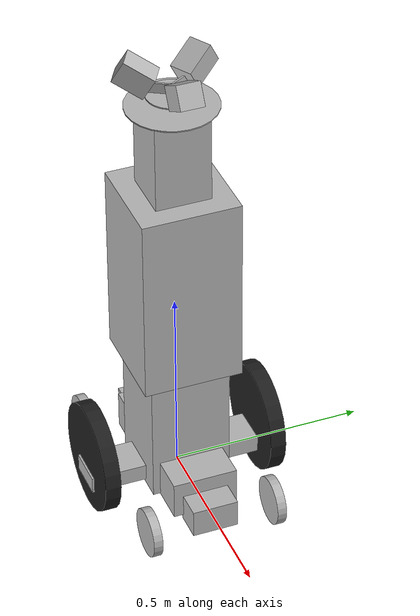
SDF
<?xml version='1.0'?>
<sdf version='1.6'>
  <model name='sq2_ccv'>
    <link name='base_footprint'>
      <pose frame=''>0 0 0 0 -0 0</pose>
      <inertial>
        <pose frame=''>0 0 -0.0055 0 -0 0</pose>
        <mass>10</mass>
        <inertia>
          <ixx>0.158391</ixx>
          <ixy>0</ixy>
          <ixz>0</ixz>
          <iyy>0.0514783</iyy>
          <iyz>0</iyz>
          <izz>0.115276</izz>
        </inertia>
      </inertial>
      <velocity_decay/>
      <gravity>1</gravity>
      <velocity_decay/>
      <self_collide>0</self_collide>
      <enable_wind>0</enable_wind>
      <kinematic>0</kinematic>
      <visual name='base_footprint_fixed_joint_lump__base_link_visual'>
        <pose frame=''>0 0 0.022 0 -0 0</pose>
        <geometry>
          <box>
            <size>0.105 0.501 0.044</size>
          </box>
        </geometry>
        <material>
          <script>
            <uri>__default__</uri>
            <name>__default__</name>
          </script>
          <shader type='pixel'/>
        </material>
        <transparency>0</transparency>
        <cast_shadows>1</cast_shadows>
      </visual>
      <visual name='base_footprint_fixed_joint_lump__base2body_link_visual_1'>
        <pose frame=''>0 0 0.034 0 -0 0</pose>
        <geometry>
          <box>
            <size>0.319 0.125 0.09</size>
          </box>
        </geometry>
        <material>
          <script>
            <uri>__default__</uri>
            <name>__default__</name>
          </script>
          <shader type='pixel'/>
        </material>
        <transparency>0</transparency>
        <cast_shadows>1</cast_shadows>
      </visual>
      <collision name='base_footprint_fixed_joint_lump__base_link_collision'>
        <laser_retro>0</laser_retro>
        <max_contacts>10</max_contacts>
        <pose frame=''>0 0 0.022 0 -0 0</pose>
        <geometry>
          <box>
            <size>0.105 0.501 0.044</size>
          </box>
        </geometry>
        <surface>
          <friction>
            <ode>
              <mu>0.05</mu>
              <mu2>0.05</mu2>
              <fdir1>0 0 0</fdir1>
              <slip1>0</slip1>
              <slip2>0</slip2>
            </ode>
            <torsional>
              <coefficient>1</coefficient>
              <patch_radius>0</patch_radius>
              <surface_radius>0</surface_radius>
              <use_patch_radius>1</use_patch_radius>
              <ode>
                <slip>0</slip>
              </ode>
            </torsional>
          </friction>
          <bounce>
            <restitution_coefficient>0</restitution_coefficient>
            <threshold>1e+06</threshold>
          </bounce>
          <contact>
            <collide_without_contact>0</collide_without_contact>
            <collide_without_contact_bitmask>1</collide_without_contact_bitmask>
            <collide_bitmask>1</collide_bitmask>
            <ode>
              <soft_cfm>0</soft_cfm>
              <soft_erp>0.2</soft_erp>
              <kp>1e+13</kp>
              <kd>1</kd>
              <max_vel>0.01</max_vel>
              <min_depth>0</min_depth>
            </ode>
            <bullet>
              <split_impulse>1</split_impulse>
              <split_impulse_penetration_threshold>-0.01</split_impulse_penetration_threshold>
              <soft_cfm>0</soft_cfm>
              <soft_erp>0.2</soft_erp>
              <kp>1e+13</kp>
              <kd>1</kd>
            </bullet>
          </contact>
        </surface>
      </collision>
      <collision name='base_footprint_fixed_joint_lump__base2body_link_collision_1'>
        <laser_retro>0</laser_retro>
        <max_contacts>10</max_contacts>
        <pose frame=''>0 0 0.034 0 -0 0</pose>
        <geometry>
          <box>
            <size>0.319 0.125 0.09</size>
          </box>
        </geometry>
        <surface>
          <friction>
            <ode>
              <mu>0.05</mu>
              <mu2>0.05</mu2>
              <fdir1>0 0 0</fdir1>
              <slip1>0</slip1>
              <slip2>0</slip2>
            </ode>
            <torsional>
              <coefficient>1</coefficient>
              <patch_radius>0</patch_radius>
              <surface_radius>0</surface_radius>
              <use_patch_radius>1</use_patch_radius>
              <ode>
                <slip>0</slip>
              </ode>
            </torsional>
          </friction>
          <bounce>
            <restitution_coefficient>0</restitution_coefficient>
            <threshold>1e+06</threshold>
          </bounce>
          <contact>
            <collide_without_contact>0</collide_without_contact>
            <collide_without_contact_bitmask>1</collide_without_contact_bitmask>
            <collide_bitmask>1</collide_bitmask>
            <ode>
              <soft_cfm>0</soft_cfm>
              <soft_erp>0.2</soft_erp>
              <kp>1e+13</kp>
              <kd>1</kd>
              <max_vel>0.01</max_vel>
              <min_depth>0</min_depth>
            </ode>
            <bullet>
              <split_impulse>1</split_impulse>
              <split_impulse_penetration_threshold>-0.01</split_impulse_penetration_threshold>
              <soft_cfm>0</soft_cfm>
              <soft_erp>0.2</soft_erp>
              <kp>1e+13</kp>
              <kd>1</kd>
            </bullet>
          </contact>
        </surface>
      </collision>
    </link>
    <link name='back_casters_pitch_link'>
      <pose frame=''>-0.1125 0 0.037 0 0 -3.14159</pose>
      <inertial>
        <pose frame=''>0.03095 0 -0.002 0 -0 0</pose>
        <mass>5</mass>
        <inertia>
          <ixx>1</ixx>
          <ixy>0</ixy>
          <ixz>0</ixz>
          <iyy>1</iyy>
          <iyz>0</iyz>
          <izz>1</izz>
        </inertia>
      </inertial>
      <gravity>1</gravity>
      <velocity_decay/>
      <self_collide>0</self_collide>
      <enable_wind>0</enable_wind>
      <kinematic>0</kinematic>
      <visual name='back_casters_pitch_link_visual'>
        <pose frame=''>0.03095 0 -0.002 0 -0 0</pose>
        <geometry>
          <box>
            <size>0.1179 0.17 0.1</size>
          </box>
        </geometry>
        <material>
          <script>
            <uri>__default__</uri>
            <name>__default__</name>
          </script>
          <shader type='pixel'/>
        </material>
        <transparency>0</transparency>
        <cast_shadows>1</cast_shadows>
      </visual>
      <collision name='back_casters_pitch_link_collision'>
        <laser_retro>0</laser_retro>
        <max_contacts>10</max_contacts>
        <pose frame=''>0.03095 0 -0.002 0 -0 0</pose>
        <geometry>
          <box>
            <size>0.1179 0.17 0.1</size>
          </box>
        </geometry>
        <surface>
          <friction>
            <ode>
              <mu>0.05</mu>
              <mu2>0.05</mu2>
              <fdir1>0 0 0</fdir1>
              <slip1>0</slip1>
              <slip2>0</slip2>
            </ode>
            <torsional>
              <coefficient>1</coefficient>
              <patch_radius>0</patch_radius>
              <surface_radius>0</surface_radius>
              <use_patch_radius>1</use_patch_radius>
              <ode>
                <slip>0</slip>
              </ode>
            </torsional>
          </friction>
          <bounce>
            <restitution_coefficient>0</restitution_coefficient>
            <threshold>1e+06</threshold>
          </bounce>
          <contact>
            <collide_without_contact>0</collide_without_contact>
            <collide_without_contact_bitmask>1</collide_without_contact_bitmask>
            <collide_bitmask>1</collide_bitmask>
            <ode>
              <soft_cfm>0</soft_cfm>
              <soft_erp>0.2</soft_erp>
              <kp>1e+13</kp>
              <kd>1</kd>
              <max_vel>0.01</max_vel>
              <min_depth>0</min_depth>
            </ode>
            <bullet>
              <split_impulse>1</split_impulse>
              <split_impulse_penetration_threshold>-0.01</split_impulse_penetration_threshold>
              <soft_cfm>0</soft_cfm>
              <soft_erp>0.2</soft_erp>
              <kp>1e+13</kp>
              <kd>1</kd>
            </bullet>
          </contact>
        </surface>
      </collision>
    </link>
    <link name='back_pitch2shaft_link'>
      <pose frame=''>-0.2024 0 0.007 0 0 -3.14159</pose>
      <inertial>
        <pose frame=''>0.034393 0 -0.002857 0 -0 0</pose>
        <mass>7</mass>
        <inertia>
          <ixx>1.05803</ixx>
          <ixy>0</ixy>
          <ixz>0.000172143</ixz>
          <iyy>1.00438</iyy>
          <iyz>8.29592e-11</iyz>
          <izz>1.0581</izz>
        </inertia>
      </inertial>
      <velocity_decay/>
      <velocity_decay/>
      <gravity>1</gravity>
      <velocity_decay/>
      <self_collide>0</self_collide>
      <enable_wind>0</enable_wind>
      <kinematic>0</kinematic>
      <visual name='back_pitch2shaft_link_visual'>
        <pose frame=''>0.03095 0 0 0 -0 0</pose>
        <geometry>
          <box>
            <size>0.078 0.12 0.074</size>
          </box>
        </geometry>
        <material>
          <script>
            <uri>__default__</uri>
            <name>__default__</name>
          </script>
          <shader type='pixel'/>
        </material>
        <transparency>0</transparency>
        <cast_shadows>1</cast_shadows>
      </visual>
      <visual name='back_pitch2shaft_link_fixed_joint_lump__back_left_caster_link_visual_1'>
        <pose frame=''>0.043 0.167 -0.01 1.5708 -0 0</pose>
        <geometry>
          <cylinder>
            <length>0.024</length>
            <radius>0.0635</radius>
          </cylinder>
        </geometry>
        <material>
          <script>
            <uri>__default__</uri>
            <name>__default__</name>
          </script>
          <shader type='pixel'/>
        </material>
        <transparency>0</transparency>
        <cast_shadows>1</cast_shadows>
      </visual>
      <visual name='back_pitch2shaft_link_fixed_joint_lump__back_right_caster_link_visual_2'>
        <pose frame=''>0.043 -0.167 -0.01 1.5708 -0 0</pose>
        <geometry>
          <cylinder>
            <length>0.024</length>
            <radius>0.0635</radius>
          </cylinder>
        </geometry>
        <material>
          <script>
            <uri>__default__</uri>
            <name>__default__</name>
          </script>
          <shader type='pixel'/>
        </material>
        <transparency>0</transparency>
        <cast_shadows>1</cast_shadows>
      </visual>
      <collision name='back_pitch2shaft_link_collision'>
        <laser_retro>0</laser_retro>
        <max_contacts>10</max_contacts>
        <pose frame=''>0.03095 0 0 0 -0 0</pose>
        <geometry>
          <box>
            <size>0.078 0.12 0.074</size>
          </box>
        </geometry>
        <surface>
          <friction>
            <ode>
              <mu>0.05</mu>
              <mu2>0.05</mu2>
              <fdir1>0 0 0</fdir1>
              <slip1>0</slip1>
              <slip2>0</slip2>
            </ode>
            <torsional>
              <coefficient>1</coefficient>
              <patch_radius>0</patch_radius>
              <surface_radius>0</surface_radius>
              <use_patch_radius>1</use_patch_radius>
              <ode>
                <slip>0</slip>
              </ode>
            </torsional>
          </friction>
          <bounce>
            <restitution_coefficient>0</restitution_coefficient>
            <threshold>1e+06</threshold>
          </bounce>
          <contact>
            <collide_without_contact>0</collide_without_contact>
            <collide_without_contact_bitmask>1</collide_without_contact_bitmask>
            <collide_bitmask>1</collide_bitmask>
            <ode>
              <soft_cfm>0</soft_cfm>
              <soft_erp>0.2</soft_erp>
              <kp>1e+13</kp>
              <kd>1</kd>
              <max_vel>0.01</max_vel>
              <min_depth>0</min_depth>
            </ode>
            <bullet>
              <split_impulse>1</split_impulse>
              <split_impulse_penetration_threshold>-0.01</split_impulse_penetration_threshold>
              <soft_cfm>0</soft_cfm>
              <soft_erp>0.2</soft_erp>
              <kp>1e+13</kp>
              <kd>1</kd>
            </bullet>
          </contact>
        </surface>
      </collision>
      <collision name='back_pitch2shaft_link_fixed_joint_lump__back_left_caster_link_collision_1'>
        <laser_retro>0</laser_retro>
        <max_contacts>10</max_contacts>
        <pose frame=''>0.043 0.167 -0.01 1.5708 -0 0</pose>
        <geometry>
          <cylinder>
            <radius>0.0635</radius>
            <length>0.024</length>
          </cylinder>
        </geometry>
        <surface>
          <friction>
            <ode>
              <mu>0</mu>
              <mu2>0</mu2>
              <fdir1>0 0 0</fdir1>
              <slip1>0</slip1>
              <slip2>0</slip2>
            </ode>
            <torsional>
              <coefficient>1</coefficient>
              <patch_radius>0</patch_radius>
              <surface_radius>0</surface_radius>
              <use_patch_radius>1</use_patch_radius>
              <ode>
                <slip>0</slip>
              </ode>
            </torsional>
          </friction>
          <bounce>
            <restitution_coefficient>0</restitution_coefficient>
            <threshold>1e+06</threshold>
          </bounce>
          <contact>
            <collide_without_contact>0</collide_without_contact>
            <collide_without_contact_bitmask>1</collide_without_contact_bitmask>
            <collide_bitmask>1</collide_bitmask>
            <ode>
              <soft_cfm>0</soft_cfm>
              <soft_erp>0.2</soft_erp>
              <kp>1e+13</kp>
              <kd>1</kd>
              <max_vel>0.01</max_vel>
              <min_depth>0</min_depth>
            </ode>
            <bullet>
              <split_impulse>1</split_impulse>
              <split_impulse_penetration_threshold>-0.01</split_impulse_penetration_threshold>
              <soft_cfm>0</soft_cfm>
              <soft_erp>0.2</soft_erp>
              <kp>1e+13</kp>
              <kd>1</kd>
            </bullet>
          </contact>
        </surface>
      </collision>
      <collision name='back_pitch2shaft_link_fixed_joint_lump__back_right_caster_link_collision_2'>
        <laser_retro>0</laser_retro>
        <max_contacts>10</max_contacts>
        <pose frame=''>0.043 -0.167 -0.01 1.5708 -0 0</pose>
        <geometry>
          <cylinder>
            <radius>0.0635</radius>
            <length>0.024</length>
          </cylinder>
        </geometry>
        <surface>
          <friction>
            <ode>
              <mu>0</mu>
              <mu2>0</mu2>
              <fdir1>0 0 0</fdir1>
              <slip1>0</slip1>
              <slip2>0</slip2>
            </ode>
            <torsional>
              <coefficient>1</coefficient>
              <patch_radius>0</patch_radius>
              <surface_radius>0</surface_radius>
              <use_patch_radius>1</use_patch_radius>
              <ode>
                <slip>0</slip>
              </ode>
            </torsional>
          </friction>
          <bounce>
            <restitution_coefficient>0</restitution_coefficient>
            <threshold>1e+06</threshold>
          </bounce>
          <contact>
            <collide_without_contact>0</collide_without_contact>
            <collide_without_contact_bitmask>1</collide_without_contact_bitmask>
            <collide_bitmask>1</collide_bitmask>
            <ode>
              <soft_cfm>0</soft_cfm>
              <soft_erp>0.2</soft_erp>
              <kp>1e+13</kp>
              <kd>1</kd>
              <max_vel>0.01</max_vel>
              <min_depth>0</min_depth>
            </ode>
            <bullet>
              <split_impulse>1</split_impulse>
              <split_impulse_penetration_threshold>-0.01</split_impulse_penetration_threshold>
              <soft_cfm>0</soft_cfm>
              <soft_erp>0.2</soft_erp>
              <kp>1e+13</kp>
              <kd>1</kd>
            </bullet>
          </contact>
        </surface>
      </collision>
    </link>
    <link name='battery_box_link'>
      <pose frame=''>-0 0 0.017 0 -0 0</pose>
      <inertial>
        <pose frame=''>0 0 0.514202 0 -0 0</pose>
        <mass>30.6</mass>
        <inertia>
          <ixx>7.07861</ixx>
          <ixy>0</ixy>
          <ixz>0</ixz>
          <iyy>7.07861</iyy>
          <iyz>0</iyz>
          <izz>3.00213</izz>
        </inertia>
      </inertial>
      <velocity_decay/>
      <velocity_decay/>
      <velocity_decay/>
      <velocity_decay/>
      <gravity>1</gravity>
      <velocity_decay/>
      <self_collide>0</self_collide>
      <enable_wind>0</enable_wind>
      <kinematic>0</kinematic>
      <visual name='battery_box_link_visual'>
        <pose frame=''>0 0 0.24675 0 -0 0</pose>
        <geometry>
          <box>
            <size>0.208 0.208 0.5535</size>
          </box>
        </geometry>
        <material>
          <script>
            <uri>__default__</uri>
            <name>__default__</name>
          </script>
          <shader type='pixel'/>
        </material>
        <transparency>0</transparency>
        <cast_shadows>1</cast_shadows>
      </visual>
      <visual name='battery_box_link_fixed_joint_lump__upper_body_link_visual_1'>
        <pose frame=''>0 0 0.569 0 -0 0</pose>
        <geometry>
          <box>
            <size>0.258 0.258 0.508</size>
          </box>
        </geometry>
        <material>
          <script>
            <uri>__default__</uri>
            <name>__default__</name>
          </script>
          <shader type='pixel'/>
        </material>
        <transparency>0</transparency>
        <cast_shadows>1</cast_shadows>
      </visual>
      <visual name='battery_box_link_fixed_joint_lump__lidar_pillar_link_visual_2'>
        <pose frame=''>0 0 0.942 0 -0 0</pose>
        <geometry>
          <box>
            <size>0.145 0.145 0.238</size>
          </box>
        </geometry>
        <material>
          <script>
            <uri>__default__</uri>
            <name>__default__</name>
          </script>
          <shader type='pixel'/>
        </material>
        <transparency>0</transparency>
        <cast_shadows>1</cast_shadows>
      </visual>
      <visual name='battery_box_link_fixed_joint_lump__centerlaser_visual_3'>
        <pose frame=''>0 0 1.0652 0 -0 0</pose>
        <geometry>
          <cylinder>
            <length>0.003</length>
            <radius>0.1175</radius>
          </cylinder>
        </geometry>
        <material>
          <script>
            <uri>__default__</uri>
            <name>__default__</name>
          </script>
          <shader type='pixel'/>
        </material>
        <transparency>0</transparency>
        <cast_shadows>1</cast_shadows>
      </visual>
      <visual name='battery_box_link_fixed_joint_lump__lidar_motor_visual_4'>
        <pose frame=''>0 0 1.06674 0 -0 0</pose>
        <geometry>
          <cylinder>
            <length>0.04908</length>
            <radius>0.02</radius>
          </cylinder>
        </geometry>
        <material>
          <script>
            <uri>__default__</uri>
            <name>__default__</name>
          </script>
          <shader type='pixel'/>
        </material>
        <transparency>0</transparency>
        <cast_shadows>1</cast_shadows>
      </visual>
      <collision name='battery_box_link_collision'>
        <laser_retro>0</laser_retro>
        <max_contacts>10</max_contacts>
        <pose frame=''>0 0 0.24675 0 -0 0</pose>
        <geometry>
          <box>
            <size>0.208 0.208 0.5535</size>
          </box>
        </geometry>
        <surface>
          <friction>
            <ode>
              <mu>0.05</mu>
              <mu2>0.05</mu2>
              <fdir1>0 0 0</fdir1>
              <slip1>0</slip1>
              <slip2>0</slip2>
            </ode>
            <torsional>
              <coefficient>1</coefficient>
              <patch_radius>0</patch_radius>
              <surface_radius>0</surface_radius>
              <use_patch_radius>1</use_patch_radius>
              <ode>
                <slip>0</slip>
              </ode>
            </torsional>
          </friction>
          <bounce>
            <restitution_coefficient>0</restitution_coefficient>
            <threshold>1e+06</threshold>
          </bounce>
          <contact>
            <collide_without_contact>0</collide_without_contact>
            <collide_without_contact_bitmask>1</collide_without_contact_bitmask>
            <collide_bitmask>1</collide_bitmask>
            <ode>
              <soft_cfm>0</soft_cfm>
              <soft_erp>0.2</soft_erp>
              <kp>1e+13</kp>
              <kd>1</kd>
              <max_vel>0.01</max_vel>
              <min_depth>0</min_depth>
            </ode>
            <bullet>
              <split_impulse>1</split_impulse>
              <split_impulse_penetration_threshold>-0.01</split_impulse_penetration_threshold>
              <soft_cfm>0</soft_cfm>
              <soft_erp>0.2</soft_erp>
              <kp>1e+13</kp>
              <kd>1</kd>
            </bullet>
          </contact>
        </surface>
      </collision>
      <collision name='battery_box_link_fixed_joint_lump__upper_body_link_collision_1'>
        <laser_retro>0</laser_retro>
        <max_contacts>10</max_contacts>
        <pose frame=''>0 0 0.569 0 -0 0</pose>
        <geometry>
          <box>
            <size>0.258 0.258 0.508</size>
          </box>
        </geometry>
        <surface>
          <friction>
            <ode>
              <mu>0.05</mu>
              <mu2>0.05</mu2>
              <fdir1>0 0 0</fdir1>
              <slip1>0</slip1>
              <slip2>0</slip2>
            </ode>
            <torsional>
              <coefficient>1</coefficient>
              <patch_radius>0</patch_radius>
              <surface_radius>0</surface_radius>
              <use_patch_radius>1</use_patch_radius>
              <ode>
                <slip>0</slip>
              </ode>
            </torsional>
          </friction>
          <bounce>
            <restitution_coefficient>0</restitution_coefficient>
            <threshold>1e+06</threshold>
          </bounce>
          <contact>
            <collide_without_contact>0</collide_without_contact>
            <collide_without_contact_bitmask>1</collide_without_contact_bitmask>
            <collide_bitmask>1</collide_bitmask>
            <ode>
              <soft_cfm>0</soft_cfm>
              <soft_erp>0.2</soft_erp>
              <kp>1e+13</kp>
              <kd>1</kd>
              <max_vel>0.01</max_vel>
              <min_depth>0</min_depth>
            </ode>
            <bullet>
              <split_impulse>1</split_impulse>
              <split_impulse_penetration_threshold>-0.01</split_impulse_penetration_threshold>
              <soft_cfm>0</soft_cfm>
              <soft_erp>0.2</soft_erp>
              <kp>1e+13</kp>
              <kd>1</kd>
            </bullet>
          </contact>
        </surface>
      </collision>
      <collision name='battery_box_link_fixed_joint_lump__lidar_pillar_link_collision_2'>
        <laser_retro>0</laser_retro>
        <max_contacts>10</max_contacts>
        <pose frame=''>0 0 0.942 0 -0 0</pose>
        <geometry>
          <box>
            <size>0.145 0.145 0.238</size>
          </box>
        </geometry>
        <surface>
          <friction>
            <ode>
              <mu>0.05</mu>
              <mu2>0.05</mu2>
              <fdir1>0 0 0</fdir1>
              <slip1>0</slip1>
              <slip2>0</slip2>
            </ode>
            <torsional>
              <coefficient>1</coefficient>
              <patch_radius>0</patch_radius>
              <surface_radius>0</surface_radius>
              <use_patch_radius>1</use_patch_radius>
              <ode>
                <slip>0</slip>
              </ode>
            </torsional>
          </friction>
          <bounce>
            <restitution_coefficient>0</restitution_coefficient>
            <threshold>1e+06</threshold>
          </bounce>
          <contact>
            <collide_without_contact>0</collide_without_contact>
            <collide_without_contact_bitmask>1</collide_without_contact_bitmask>
            <collide_bitmask>1</collide_bitmask>
            <ode>
              <soft_cfm>0</soft_cfm>
              <soft_erp>0.2</soft_erp>
              <kp>1e+13</kp>
              <kd>1</kd>
              <max_vel>0.01</max_vel>
              <min_depth>0</min_depth>
            </ode>
            <bullet>
              <split_impulse>1</split_impulse>
              <split_impulse_penetration_threshold>-0.01</split_impulse_penetration_threshold>
              <soft_cfm>0</soft_cfm>
              <soft_erp>0.2</soft_erp>
              <kp>1e+13</kp>
              <kd>1</kd>
            </bullet>
          </contact>
        </surface>
      </collision>
      <collision name='battery_box_link_fixed_joint_lump__centerlaser_collision_3'>
        <laser_retro>0</laser_retro>
        <max_contacts>10</max_contacts>
        <pose frame=''>0 0 1.0652 0 -0 0</pose>
        <geometry>
          <cylinder>
            <radius>0.1175</radius>
            <length>0.003</length>
          </cylinder>
        </geometry>
        <surface>
          <friction>
            <ode>
              <mu>0.05</mu>
              <mu2>0.05</mu2>
              <fdir1>0 0 0</fdir1>
              <slip1>0</slip1>
              <slip2>0</slip2>
            </ode>
            <torsional>
              <coefficient>1</coefficient>
              <patch_radius>0</patch_radius>
              <surface_radius>0</surface_radius>
              <use_patch_radius>1</use_patch_radius>
              <ode>
                <slip>0</slip>
              </ode>
            </torsional>
          </friction>
          <bounce>
            <restitution_coefficient>0</restitution_coefficient>
            <threshold>1e+06</threshold>
          </bounce>
          <contact>
            <collide_without_contact>0</collide_without_contact>
            <collide_without_contact_bitmask>1</collide_without_contact_bitmask>
            <collide_bitmask>1</collide_bitmask>
            <ode>
              <soft_cfm>0</soft_cfm>
              <soft_erp>0.2</soft_erp>
              <kp>1e+13</kp>
              <kd>1</kd>
              <max_vel>0.01</max_vel>
              <min_depth>0</min_depth>
            </ode>
            <bullet>
              <split_impulse>1</split_impulse>
              <split_impulse_penetration_threshold>-0.01</split_impulse_penetration_threshold>
              <soft_cfm>0</soft_cfm>
              <soft_erp>0.2</soft_erp>
              <kp>1e+13</kp>
              <kd>1</kd>
            </bullet>
          </contact>
        </surface>
      </collision>
      <collision name='battery_box_link_fixed_joint_lump__lidar_motor_collision_4'>
        <laser_retro>0</laser_retro>
        <max_contacts>10</max_contacts>
        <pose frame=''>0 0 1.06674 0 -0 0</pose>
        <geometry>
          <cylinder>
            <radius>0.02</radius>
            <length>0.04908</length>
          </cylinder>
        </geometry>
        <surface>
          <friction>
            <ode>
              <mu>0.05</mu>
              <mu2>0.05</mu2>
              <fdir1>0 0 0</fdir1>
              <slip1>0</slip1>
              <slip2>0</slip2>
            </ode>
            <torsional>
              <coefficient>1</coefficient>
              <patch_radius>0</patch_radius>
              <surface_radius>0</surface_radius>
              <use_patch_radius>1</use_patch_radius>
              <ode>
                <slip>0</slip>
              </ode>
            </torsional>
          </friction>
          <bounce>
            <restitution_coefficient>0</restitution_coefficient>
            <threshold>1e+06</threshold>
          </bounce>
          <contact>
            <collide_without_contact>0</collide_without_contact>
            <collide_without_contact_bitmask>1</collide_without_contact_bitmask>
            <collide_bitmask>1</collide_bitmask>
            <ode>
              <soft_cfm>0</soft_cfm>
              <soft_erp>0.2</soft_erp>
              <kp>1e+13</kp>
              <kd>1</kd>
              <max_vel>0.01</max_vel>
              <min_depth>0</min_depth>
            </ode>
            <bullet>
              <split_impulse>1</split_impulse>
              <split_impulse_penetration_threshold>-0.01</split_impulse_penetration_threshold>
              <soft_cfm>0</soft_cfm>
              <soft_erp>0.2</soft_erp>
              <kp>1e+13</kp>
              <kd>1</kd>
            </bullet>
          </contact>
        </surface>
      </collision>
    </link>
    <link name='front_casters_pitch_link'>
      <pose frame=''>0.1125 0 0.037 0 -0 0</pose>
      <inertial>
        <pose frame=''>0.03095 0 -0.002 0 -0 0</pose>
        <mass>5</mass>
        <inertia>
          <ixx>1</ixx>
          <ixy>0</ixy>
          <ixz>0</ixz>
          <iyy>1</iyy>
          <iyz>0</iyz>
          <izz>1</izz>
        </inertia>
      </inertial>
      <gravity>1</gravity>
      <velocity_decay/>
      <self_collide>0</self_collide>
      <enable_wind>0</enable_wind>
      <kinematic>0</kinematic>
      <visual name='front_casters_pitch_link_visual'>
        <pose frame=''>0.03095 0 -0.002 0 -0 0</pose>
        <geometry>
          <box>
            <size>0.1179 0.17 0.1</size>
          </box>
        </geometry>
        <material>
          <script>
            <uri>__default__</uri>
            <name>__default__</name>
          </script>
          <shader type='pixel'/>
        </material>
        <transparency>0</transparency>
        <cast_shadows>1</cast_shadows>
      </visual>
      <collision name='front_casters_pitch_link_collision'>
        <laser_retro>0</laser_retro>
        <max_contacts>10</max_contacts>
        <pose frame=''>0.03095 0 -0.002 0 -0 0</pose>
        <geometry>
          <box>
            <size>0.1179 0.17 0.1</size>
          </box>
        </geometry>
        <surface>
          <friction>
            <ode>
              <mu>0.05</mu>
              <mu2>0.05</mu2>
              <fdir1>0 0 0</fdir1>
              <slip1>0</slip1>
              <slip2>0</slip2>
            </ode>
            <torsional>
              <coefficient>1</coefficient>
              <patch_radius>0</patch_radius>
              <surface_radius>0</surface_radius>
              <use_patch_radius>1</use_patch_radius>
              <ode>
                <slip>0</slip>
              </ode>
            </torsional>
          </friction>
          <bounce>
            <restitution_coefficient>0</restitution_coefficient>
            <threshold>1e+06</threshold>
          </bounce>
          <contact>
            <collide_without_contact>0</collide_without_contact>
            <collide_without_contact_bitmask>1</collide_without_contact_bitmask>
            <collide_bitmask>1</collide_bitmask>
            <ode>
              <soft_cfm>0</soft_cfm>
              <soft_erp>0.2</soft_erp>
              <kp>1e+13</kp>
              <kd>1</kd>
              <max_vel>0.01</max_vel>
              <min_depth>0</min_depth>
            </ode>
            <bullet>
              <split_impulse>1</split_impulse>
              <split_impulse_penetration_threshold>-0.01</split_impulse_penetration_threshold>
              <soft_cfm>0</soft_cfm>
              <soft_erp>0.2</soft_erp>
              <kp>1e+13</kp>
              <kd>1</kd>
            </bullet>
          </contact>
        </surface>
      </collision>
    </link>
    <link name='front_pitch2shaft_link'>
      <pose frame=''>0.2024 -0 0.007 0 -0 0</pose>
      <inertial>
        <pose frame=''>0.034393 0 -0.002857 0 -0 0</pose>
        <mass>7</mass>
        <inertia>
          <ixx>1.05803</ixx>
          <ixy>0</ixy>
          <ixz>0.000172143</ixz>
          <iyy>1.00438</iyy>
          <iyz>8.29592e-11</iyz>
          <izz>1.0581</izz>
        </inertia>
      </inertial>
      <velocity_decay/>
      <velocity_decay/>
      <gravity>1</gravity>
      <velocity_decay/>
      <self_collide>0</self_collide>
      <enable_wind>0</enable_wind>
      <kinematic>0</kinematic>
      <visual name='front_pitch2shaft_link_visual'>
        <pose frame=''>0.03095 0 0 0 -0 0</pose>
        <geometry>
          <box>
            <size>0.078 0.12 0.074</size>
          </box>
        </geometry>
        <material>
          <script>
            <uri>__default__</uri>
            <name>__default__</name>
          </script>
          <shader type='pixel'/>
        </material>
        <transparency>0</transparency>
        <cast_shadows>1</cast_shadows>
      </visual>
      <visual name='front_pitch2shaft_link_fixed_joint_lump__front_left_caster_link_visual_1'>
        <pose frame=''>0.043 0.167 -0.01 1.5708 -0 0</pose>
        <geometry>
          <cylinder>
            <length>0.024</length>
            <radius>0.0635</radius>
          </cylinder>
        </geometry>
        <material>
          <script>
            <uri>__default__</uri>
            <name>__default__</name>
          </script>
          <shader type='pixel'/>
        </material>
        <transparency>0</transparency>
        <cast_shadows>1</cast_shadows>
      </visual>
      <visual name='front_pitch2shaft_link_fixed_joint_lump__front_right_caster_link_visual_2'>
        <pose frame=''>0.043 -0.167 -0.01 1.5708 -0 0</pose>
        <geometry>
          <cylinder>
            <length>0.024</length>
            <radius>0.0635</radius>
          </cylinder>
        </geometry>
        <material>
          <script>
            <uri>__default__</uri>
            <name>__default__</name>
          </script>
          <shader type='pixel'/>
        </material>
        <transparency>0</transparency>
        <cast_shadows>1</cast_shadows>
      </visual>
      <collision name='front_pitch2shaft_link_collision'>
        <laser_retro>0</laser_retro>
        <max_contacts>10</max_contacts>
        <pose frame=''>0.03095 0 0 0 -0 0</pose>
        <geometry>
          <box>
            <size>0.078 0.12 0.074</size>
          </box>
        </geometry>
        <surface>
          <friction>
            <ode>
              <mu>0.05</mu>
              <mu2>0.05</mu2>
              <fdir1>0 0 0</fdir1>
              <slip1>0</slip1>
              <slip2>0</slip2>
            </ode>
            <torsional>
              <coefficient>1</coefficient>
              <patch_radius>0</patch_radius>
              <surface_radius>0</surface_radius>
              <use_patch_radius>1</use_patch_radius>
              <ode>
                <slip>0</slip>
              </ode>
            </torsional>
          </friction>
          <bounce>
            <restitution_coefficient>0</restitution_coefficient>
            <threshold>1e+06</threshold>
          </bounce>
          <contact>
            <collide_without_contact>0</collide_without_contact>
            <collide_without_contact_bitmask>1</collide_without_contact_bitmask>
            <collide_bitmask>1</collide_bitmask>
            <ode>
              <soft_cfm>0</soft_cfm>
              <soft_erp>0.2</soft_erp>
              <kp>1e+13</kp>
              <kd>1</kd>
              <max_vel>0.01</max_vel>
              <min_depth>0</min_depth>
            </ode>
            <bullet>
              <split_impulse>1</split_impulse>
              <split_impulse_penetration_threshold>-0.01</split_impulse_penetration_threshold>
              <soft_cfm>0</soft_cfm>
              <soft_erp>0.2</soft_erp>
              <kp>1e+13</kp>
              <kd>1</kd>
            </bullet>
          </contact>
        </surface>
      </collision>
      <collision name='front_pitch2shaft_link_fixed_joint_lump__front_left_caster_link_collision_1'>
        <laser_retro>0</laser_retro>
        <max_contacts>10</max_contacts>
        <pose frame=''>0.043 0.167 -0.01 1.5708 -0 0</pose>
        <geometry>
          <cylinder>
            <radius>0.0635</radius>
            <length>0.024</length>
          </cylinder>
        </geometry>
        <surface>
          <friction>
            <ode>
              <mu>0</mu>
              <mu2>0</mu2>
              <fdir1>0 0 0</fdir1>
              <slip1>0</slip1>
              <slip2>0</slip2>
            </ode>
            <torsional>
              <coefficient>1</coefficient>
              <patch_radius>0</patch_radius>
              <surface_radius>0</surface_radius>
              <use_patch_radius>1</use_patch_radius>
              <ode>
                <slip>0</slip>
              </ode>
            </torsional>
          </friction>
          <bounce>
            <restitution_coefficient>0</restitution_coefficient>
            <threshold>1e+06</threshold>
          </bounce>
          <contact>
            <collide_without_contact>0</collide_without_contact>
            <collide_without_contact_bitmask>1</collide_without_contact_bitmask>
            <collide_bitmask>1</collide_bitmask>
            <ode>
              <soft_cfm>0</soft_cfm>
              <soft_erp>0.2</soft_erp>
              <kp>1e+13</kp>
              <kd>1</kd>
              <max_vel>0.01</max_vel>
              <min_depth>0</min_depth>
            </ode>
            <bullet>
              <split_impulse>1</split_impulse>
              <split_impulse_penetration_threshold>-0.01</split_impulse_penetration_threshold>
              <soft_cfm>0</soft_cfm>
              <soft_erp>0.2</soft_erp>
              <kp>1e+13</kp>
              <kd>1</kd>
            </bullet>
          </contact>
        </surface>
      </collision>
      <collision name='front_pitch2shaft_link_fixed_joint_lump__front_right_caster_link_collision_2'>
        <laser_retro>0</laser_retro>
        <max_contacts>10</max_contacts>
        <pose frame=''>0.043 -0.167 -0.01 1.5708 -0 0</pose>
        <geometry>
          <cylinder>
            <radius>0.0635</radius>
            <length>0.024</length>
          </cylinder>
        </geometry>
        <surface>
          <friction>
            <ode>
              <mu>0</mu>
              <mu2>0</mu2>
              <fdir1>0 0 0</fdir1>
              <slip1>0</slip1>
              <slip2>0</slip2>
            </ode>
            <torsional>
              <coefficient>1</coefficient>
              <patch_radius>0</patch_radius>
              <surface_radius>0</surface_radius>
              <use_patch_radius>1</use_patch_radius>
              <ode>
                <slip>0</slip>
              </ode>
            </torsional>
          </friction>
          <bounce>
            <restitution_coefficient>0</restitution_coefficient>
            <threshold>1e+06</threshold>
          </bounce>
          <contact>
            <collide_without_contact>0</collide_without_contact>
            <collide_without_contact_bitmask>1</collide_without_contact_bitmask>
            <collide_bitmask>1</collide_bitmask>
            <ode>
              <soft_cfm>0</soft_cfm>
              <soft_erp>0.2</soft_erp>
              <kp>1e+13</kp>
              <kd>1</kd>
              <max_vel>0.01</max_vel>
              <min_depth>0</min_depth>
            </ode>
            <bullet>
              <split_impulse>1</split_impulse>
              <split_impulse_penetration_threshold>-0.01</split_impulse_penetration_threshold>
              <soft_cfm>0</soft_cfm>
              <soft_erp>0.2</soft_erp>
              <kp>1e+13</kp>
              <kd>1</kd>
            </bullet>
          </contact>
        </surface>
      </collision>
    </link>
    <link name='left_steering_link'>
      <pose frame=''>0 0.2245 0.048 0 -0 0</pose>
      <inertial>
        <pose frame=''>0 0 0.0015 0 -0 0</pose>
        <mass>1</mass>
        <inertia>
          <ixx>7.08906e-05</ixx>
          <ixy>0</ixy>
          <ixz>0</ixz>
          <iyy>7.08906e-05</iyy>
          <iyz>0</iyz>
          <izz>0.000140281</izz>
        </inertia>
      </inertial>
      <gravity>1</gravity>
      <velocity_decay/>
      <self_collide>0</self_collide>
      <enable_wind>0</enable_wind>
      <kinematic>0</kinematic>
      <visual name='left_steering_link_visual'>
        <pose frame=''>0 0 0.0015 0 -0 0</pose>
        <geometry>
          <cylinder>
            <length>0.003</length>
            <radius>0.01675</radius>
          </cylinder>
        </geometry>
        <material>
          <script>
            <uri>__default__</uri>
            <name>__default__</name>
          </script>
          <shader type='pixel'/>
        </material>
        <transparency>0</transparency>
        <cast_shadows>1</cast_shadows>
      </visual>
      <collision name='left_steering_link_collision'>
        <laser_retro>0</laser_retro>
        <max_contacts>10</max_contacts>
        <pose frame=''>0 0 0.0015 0 -0 0</pose>
        <geometry>
          <cylinder>
            <radius>0.01675</radius>
            <length>0.003</length>
          </cylinder>
        </geometry>
        <surface>
          <friction>
            <ode>
              <mu>0.05</mu>
              <mu2>0.05</mu2>
              <fdir1>0 0 0</fdir1>
              <slip1>0</slip1>
              <slip2>0</slip2>
            </ode>
            <torsional>
              <coefficient>1</coefficient>
              <patch_radius>0</patch_radius>
              <surface_radius>0</surface_radius>
              <use_patch_radius>1</use_patch_radius>
              <ode>
                <slip>0</slip>
              </ode>
            </torsional>
          </friction>
          <bounce>
            <restitution_coefficient>0</restitution_coefficient>
            <threshold>1e+06</threshold>
          </bounce>
          <contact>
            <collide_without_contact>0</collide_without_contact>
            <collide_without_contact_bitmask>1</collide_without_contact_bitmask>
            <collide_bitmask>1</collide_bitmask>
            <ode>
              <soft_cfm>0</soft_cfm>
              <soft_erp>0.2</soft_erp>
              <kp>1e+13</kp>
              <kd>1</kd>
              <max_vel>0.01</max_vel>
              <min_depth>0</min_depth>
            </ode>
            <bullet>
              <split_impulse>1</split_impulse>
              <split_impulse_penetration_threshold>-0.01</split_impulse_penetration_threshold>
              <soft_cfm>0</soft_cfm>
              <soft_erp>0.2</soft_erp>
              <kp>1e+13</kp>
              <kd>1</kd>
            </bullet>
          </contact>
        </surface>
      </collision>
    </link>
    <link name='left_wheel_link'>
      <pose frame=''>0 0.2245 0.0755 0 -0 0</pose>
      <inertial>
        <pose frame=''>0 0 0 1.5708 -0 0</pose>
        <mass>5</mass>
        <inertia>
          <ixx>0.0264579</ixx>
          <ixy>0</ixy>
          <ixz>0</ixz>
          <iyy>0.0264579</iyy>
          <iyz>0</iyz>
          <izz>0.0514806</izz>
        </inertia>
      </inertial>
      <gravity>1</gravity>
      <velocity_decay/>
      <self_collide>0</self_collide>
      <enable_wind>0</enable_wind>
      <kinematic>0</kinematic>
      <visual name='left_wheel_link_visual'>
        <pose frame=''>0 0 0 1.5708 -0 0</pose>
        <geometry>
          <cylinder>
            <length>0.0415</length>
            <radius>0.1435</radius>
          </cylinder>
        </geometry>
        <material>
          <script>
            <name>Gazebo/Black</name>
            <uri>file://media/materials/scripts/gazebo.material</uri>
          </script>
          <shader type='pixel'/>
        </material>
        <transparency>0</transparency>
        <cast_shadows>1</cast_shadows>
      </visual>
      <collision name='left_wheel_link_collision'>
        <laser_retro>0</laser_retro>
        <max_contacts>10</max_contacts>
        <pose frame=''>0 0 0 1.5708 -0 0</pose>
        <geometry>
          <cylinder>
            <radius>0.1435</radius>
            <length>0.0415</length>
          </cylinder>
        </geometry>
        <surface>
          <friction>
            <ode>
              <mu>0.8</mu>
              <mu2>0.8</mu2>
              <fdir1>0 0 0</fdir1>
              <slip1>0</slip1>
              <slip2>0</slip2>
            </ode>
            <torsional>
              <coefficient>1</coefficient>
              <patch_radius>0</patch_radius>
              <surface_radius>0</surface_radius>
              <use_patch_radius>1</use_patch_radius>
              <ode>
                <slip>0</slip>
              </ode>
            </torsional>
          </friction>
          <bounce>
            <restitution_coefficient>0</restitution_coefficient>
            <threshold>1e+06</threshold>
          </bounce>
          <contact>
            <collide_without_contact>0</collide_without_contact>
            <collide_without_contact_bitmask>1</collide_without_contact_bitmask>
            <collide_bitmask>1</collide_bitmask>
            <ode>
              <soft_cfm>0</soft_cfm>
              <soft_erp>0.2</soft_erp>
              <kp>1e+13</kp>
              <kd>1</kd>
              <max_vel>0.01</max_vel>
              <min_depth>0</min_depth>
            </ode>
            <bullet>
              <split_impulse>1</split_impulse>
              <split_impulse_penetration_threshold>-0.01</split_impulse_penetration_threshold>
              <soft_cfm>0</soft_cfm>
              <soft_erp>0.2</soft_erp>
              <kp>1e+13</kp>
              <kd>1</kd>
            </bullet>
          </contact>
        </surface>
      </collision>
    </link>
    <link name='right_steering_link'>
      <pose frame=''>-0 -0.2245 0.048 0 -0 0</pose>
      <inertial>
        <pose frame=''>0 0 0.0015 0 -0 0</pose>
        <mass>1</mass>
        <inertia>
          <ixx>7.08906e-05</ixx>
          <ixy>0</ixy>
          <ixz>0</ixz>
          <iyy>7.08906e-05</iyy>
          <iyz>0</iyz>
          <izz>0.000140281</izz>
        </inertia>
      </inertial>
      <gravity>1</gravity>
      <velocity_decay/>
      <self_collide>0</self_collide>
      <enable_wind>0</enable_wind>
      <kinematic>0</kinematic>
      <visual name='right_steering_link_visual'>
        <pose frame=''>0 0 0.0015 0 -0 0</pose>
        <geometry>
          <cylinder>
            <length>0.003</length>
            <radius>0.01675</radius>
          </cylinder>
        </geometry>
        <material>
          <script>
            <uri>__default__</uri>
            <name>__default__</name>
          </script>
          <shader type='pixel'/>
        </material>
        <transparency>0</transparency>
        <cast_shadows>1</cast_shadows>
      </visual>
      <collision name='right_steering_link_collision'>
        <laser_retro>0</laser_retro>
        <max_contacts>10</max_contacts>
        <pose frame=''>0 0 0.0015 0 -0 0</pose>
        <geometry>
          <cylinder>
            <radius>0.01675</radius>
            <length>0.003</length>
          </cylinder>
        </geometry>
        <surface>
          <friction>
            <ode>
              <mu>0.05</mu>
              <mu2>0.05</mu2>
              <fdir1>0 0 0</fdir1>
              <slip1>0</slip1>
              <slip2>0</slip2>
            </ode>
            <torsional>
              <coefficient>1</coefficient>
              <patch_radius>0</patch_radius>
              <surface_radius>0</surface_radius>
              <use_patch_radius>1</use_patch_radius>
              <ode>
                <slip>0</slip>
              </ode>
            </torsional>
          </friction>
          <bounce>
            <restitution_coefficient>0</restitution_coefficient>
            <threshold>1e+06</threshold>
          </bounce>
          <contact>
            <collide_without_contact>0</collide_without_contact>
            <collide_without_contact_bitmask>1</collide_without_contact_bitmask>
            <collide_bitmask>1</collide_bitmask>
            <ode>
              <soft_cfm>0</soft_cfm>
              <soft_erp>0.2</soft_erp>
              <kp>1e+13</kp>
              <kd>1</kd>
              <max_vel>0.01</max_vel>
              <min_depth>0</min_depth>
            </ode>
            <bullet>
              <split_impulse>1</split_impulse>
              <split_impulse_penetration_threshold>-0.01</split_impulse_penetration_threshold>
              <soft_cfm>0</soft_cfm>
              <soft_erp>0.2</soft_erp>
              <kp>1e+13</kp>
              <kd>1</kd>
            </bullet>
          </contact>
        </surface>
      </collision>
    </link>
    <link name='right_wheel_link'>
      <pose frame=''>-0 -0.2245 0.0755 0 -0 0</pose>
      <inertial>
        <pose frame=''>0 0 0 1.5708 -0 0</pose>
        <mass>5</mass>
        <inertia>
          <ixx>0.0264579</ixx>
          <ixy>0</ixy>
          <ixz>0</ixz>
          <iyy>0.0264579</iyy>
          <iyz>0</iyz>
          <izz>0.0514806</izz>
        </inertia>
      </inertial>
      <gravity>1</gravity>
      <velocity_decay/>
      <self_collide>0</self_collide>
      <enable_wind>0</enable_wind>
      <kinematic>0</kinematic>
      <visual name='right_wheel_link_visual'>
        <pose frame=''>0 0 0 1.5708 -0 0</pose>
        <geometry>
          <cylinder>
            <length>0.0415</length>
            <radius>0.1435</radius>
          </cylinder>
        </geometry>
        <material>
          <script>
            <name>Gazebo/Black</name>
            <uri>file://media/materials/scripts/gazebo.material</uri>
          </script>
          <shader type='pixel'/>
        </material>
        <transparency>0</transparency>
        <cast_shadows>1</cast_shadows>
      </visual>
      <collision name='right_wheel_link_collision'>
        <laser_retro>0</laser_retro>
        <max_contacts>10</max_contacts>
        <pose frame=''>0 0 0 1.5708 -0 0</pose>
        <geometry>
          <cylinder>
            <radius>0.1435</radius>
            <length>0.0415</length>
          </cylinder>
        </geometry>
        <surface>
          <friction>
            <ode>
              <mu>0.8</mu>
              <mu2>0.8</mu2>
              <fdir1>0 0 0</fdir1>
              <slip1>0</slip1>
              <slip2>0</slip2>
            </ode>
            <torsional>
              <coefficient>1</coefficient>
              <patch_radius>0</patch_radius>
              <surface_radius>0</surface_radius>
              <use_patch_radius>1</use_patch_radius>
              <ode>
                <slip>0</slip>
              </ode>
            </torsional>
          </friction>
          <bounce>
            <restitution_coefficient>0</restitution_coefficient>
            <threshold>1e+06</threshold>
          </bounce>
          <contact>
            <collide_without_contact>0</collide_without_contact>
            <collide_without_contact_bitmask>1</collide_without_contact_bitmask>
            <collide_bitmask>1</collide_bitmask>
            <ode>
              <soft_cfm>0</soft_cfm>
              <soft_erp>0.2</soft_erp>
              <kp>1e+13</kp>
              <kd>1</kd>
              <max_vel>0.01</max_vel>
              <min_depth>0</min_depth>
            </ode>
            <bullet>
              <split_impulse>1</split_impulse>
              <split_impulse_penetration_threshold>-0.01</split_impulse_penetration_threshold>
              <soft_cfm>0</soft_cfm>
              <soft_erp>0.2</soft_erp>
              <kp>1e+13</kp>
              <kd>1</kd>
            </bullet>
          </contact>
        </surface>
      </collision>
    </link>
    <link name='turn_table'>
      <pose frame=''>-0 0 1.11028 0 -0 0</pose>
      <inertial>
        <pose frame=''>0 0 0.032157 0 -0 0</pose>
        <mass>1.5</mass>
        <inertia>
          <ixx>0.00547591</ixx>
          <ixy>-2.08976e-10</ixy>
          <ixz>-1.53742e-11</ixz>
          <iyy>0.00547591</iyy>
          <iyz>-2.66289e-11</iyz>
          <izz>0.00846687</izz>
        </inertia>
      </inertial>
      <velocity_decay/>
      <self_collide>0</self_collide>
      <velocity_decay/>
      <sensor name='laser1_lrf_sensor' type='ray'>
        <visualize>0</visualize>
        <update_rate>100</update_rate>
        <ray>
          <scan>
            <horizontal>
              <samples>416</samples>
              <resolution>1</resolution>
              <min_angle>-2.35619</min_angle>
              <max_angle>2.35619</max_angle>
            </horizontal>
            <vertical>
              <samples>1</samples>
              <min_angle>0</min_angle>
              <max_angle>0</max_angle>
            </vertical>
          </scan>
          <range>
            <min>0.1</min>
            <max>30</max>
            <resolution>0.01</resolution>
          </range>
          <noise>
            <type>gaussian</type>
            <mean>0</mean>
            <stddev>0.03</stddev>
          </noise>
        </ray>
        <pose frame=''>-0.047058 0.081507 0.05247 0 1.0472 2.0944</pose>
      </sensor>
      <velocity_decay/>
      <sensor name='laser2_lrf_sensor' type='ray'>
        <visualize>0</visualize>
        <update_rate>100</update_rate>
        <ray>
          <scan>
            <horizontal>
              <samples>416</samples>
              <resolution>1</resolution>
              <min_angle>-2.35619</min_angle>
              <max_angle>2.35619</max_angle>
            </horizontal>
            <vertical>
              <samples>1</samples>
              <min_angle>0</min_angle>
              <max_angle>0</max_angle>
            </vertical>
          </scan>
          <range>
            <min>0.1</min>
            <max>30</max>
            <resolution>0.01</resolution>
          </range>
          <noise>
            <type>gaussian</type>
            <mean>0</mean>
            <stddev>0.03</stddev>
          </noise>
        </ray>
        <pose frame=''>-0.047058 -0.081507 0.05247 0 1.0472 -2.09439</pose>
      </sensor>
      <gravity>1</gravity>
      <velocity_decay/>
      <sensor name='laser3_lrf_sensor' type='ray'>
        <visualize>0</visualize>
        <update_rate>100</update_rate>
        <ray>
          <scan>
            <horizontal>
              <samples>416</samples>
              <resolution>1</resolution>
              <min_angle>-2.35619</min_angle>
              <max_angle>2.35619</max_angle>
            </horizontal>
            <vertical>
              <samples>1</samples>
              <min_angle>0</min_angle>
              <max_angle>0</max_angle>
            </vertical>
          </scan>
          <range>
            <min>0.1</min>
            <max>30</max>
            <resolution>0.01</resolution>
          </range>
          <noise>
            <type>gaussian</type>
            <mean>0</mean>
            <stddev>0.03</stddev>
          </noise>
        </ray>
        <pose frame=''>0.094116 0 0.05247 0 1.0472 0</pose>
      </sensor>
      <enable_wind>0</enable_wind>
      <kinematic>0</kinematic>
      <visual name='turn_table_visual'>
        <pose frame=''>0 0 0.0015 0 -0 0</pose>
        <geometry>
          <cylinder>
            <length>0.003</length>
            <radius>0.065</radius>
          </cylinder>
        </geometry>
        <material>
          <script>
            <uri>__default__</uri>
            <name>__default__</name>
          </script>
          <shader type='pixel'/>
        </material>
        <transparency>0</transparency>
        <cast_shadows>1</cast_shadows>
      </visual>
      <visual name='turn_table_fixed_joint_lump__turntable2laser1_link_visual_1'>
        <pose frame=''>-0.01875 0.032476 0.015 0 -0 2.0944</pose>
        <geometry>
          <box>
            <size>0.075 0.005 0.03</size>
          </box>
        </geometry>
        <material>
          <shader type='pixel'/>
        </material>
        <transparency>0</transparency>
        <cast_shadows>1</cast_shadows>
      </visual>
      <visual name='turn_table_fixed_joint_lump__laser1_base_link_visual_2'>
        <pose frame=''>-0.043269 0.074945 0.048095 0 1.0472 2.0944</pose>
        <geometry>
          <box>
            <size>0.062 0.062 0.0875</size>
          </box>
        </geometry>
        <material>
          <shader type='pixel'/>
        </material>
        <transparency>0</transparency>
        <cast_shadows>1</cast_shadows>
      </visual>
      <visual name='turn_table_fixed_joint_lump__turntable2laser2_link_visual_3'>
        <pose frame=''>-0.01875 -0.032476 0.015 0 -0 -2.09439</pose>
        <geometry>
          <box>
            <size>0.075 0.005 0.03</size>
          </box>
        </geometry>
        <material>
          <shader type='pixel'/>
        </material>
        <transparency>0</transparency>
        <cast_shadows>1</cast_shadows>
      </visual>
      <visual name='turn_table_fixed_joint_lump__laser2_base_link_visual_4'>
        <pose frame=''>-0.043269 -0.074945 0.048095 0 1.0472 -2.09439</pose>
        <geometry>
          <box>
            <size>0.062 0.062 0.0875</size>
          </box>
        </geometry>
        <material>
          <shader type='pixel'/>
        </material>
        <transparency>0</transparency>
        <cast_shadows>1</cast_shadows>
      </visual>
      <visual name='turn_table_fixed_joint_lump__turntable2laser3_link_visual_5'>
        <pose frame=''>0.0375 0 0.015 0 -0 0</pose>
        <geometry>
          <box>
            <size>0.075 0.005 0.03</size>
          </box>
        </geometry>
        <material>
          <shader type='pixel'/>
        </material>
        <transparency>0</transparency>
        <cast_shadows>1</cast_shadows>
      </visual>
      <visual name='turn_table_fixed_joint_lump__laser3_base_link_visual_6'>
        <pose frame=''>0.086539 0 0.048095 0 1.0472 0</pose>
        <geometry>
          <box>
            <size>0.062 0.062 0.0875</size>
          </box>
        </geometry>
        <material>
          <shader type='pixel'/>
        </material>
        <transparency>0</transparency>
        <cast_shadows>1</cast_shadows>
      </visual>
      <collision name='turn_table_collision'>
        <laser_retro>0</laser_retro>
        <max_contacts>10</max_contacts>
        <pose frame=''>0 0 0.0015 0 -0 0</pose>
        <geometry>
          <cylinder>
            <radius>0.065</radius>
            <length>0.003</length>
          </cylinder>
        </geometry>
        <surface>
          <friction>
            <ode>
              <mu>0.05</mu>
              <mu2>0.05</mu2>
              <fdir1>0 0 0</fdir1>
              <slip1>0</slip1>
              <slip2>0</slip2>
            </ode>
            <torsional>
              <coefficient>1</coefficient>
              <patch_radius>0</patch_radius>
              <surface_radius>0</surface_radius>
              <use_patch_radius>1</use_patch_radius>
              <ode>
                <slip>0</slip>
              </ode>
            </torsional>
          </friction>
          <bounce>
            <restitution_coefficient>0</restitution_coefficient>
            <threshold>1e+06</threshold>
          </bounce>
          <contact>
            <collide_without_contact>0</collide_without_contact>
            <collide_without_contact_bitmask>1</collide_without_contact_bitmask>
            <collide_bitmask>1</collide_bitmask>
            <ode>
              <soft_cfm>0</soft_cfm>
              <soft_erp>0.2</soft_erp>
              <kp>1e+13</kp>
              <kd>1</kd>
              <max_vel>0.01</max_vel>
              <min_depth>0</min_depth>
            </ode>
            <bullet>
              <split_impulse>1</split_impulse>
              <split_impulse_penetration_threshold>-0.01</split_impulse_penetration_threshold>
              <soft_cfm>0</soft_cfm>
              <soft_erp>0.2</soft_erp>
              <kp>1e+13</kp>
              <kd>1</kd>
            </bullet>
          </contact>
        </surface>
      </collision>
      <collision name='turn_table_fixed_joint_lump__turntable2laser1_link_collision_1'>
        <laser_retro>0</laser_retro>
        <max_contacts>10</max_contacts>
        <pose frame=''>-0.01875 0.032476 0.015 0 -0 2.0944</pose>
        <geometry>
          <box>
            <size>0.075 0.005 0.03</size>
          </box>
        </geometry>
        <surface>
          <friction>
            <ode>
              <mu>1</mu>
              <mu2>1</mu2>
              <fdir1>0 0 0</fdir1>
              <slip1>0</slip1>
              <slip2>0</slip2>
            </ode>
            <torsional>
              <coefficient>1</coefficient>
              <patch_radius>0</patch_radius>
              <surface_radius>0</surface_radius>
              <use_patch_radius>1</use_patch_radius>
              <ode>
                <slip>0</slip>
              </ode>
            </torsional>
          </friction>
          <bounce>
            <restitution_coefficient>0</restitution_coefficient>
            <threshold>1e+06</threshold>
          </bounce>
          <contact>
            <collide_without_contact>0</collide_without_contact>
            <collide_without_contact_bitmask>1</collide_without_contact_bitmask>
            <collide_bitmask>1</collide_bitmask>
            <ode>
              <soft_cfm>0</soft_cfm>
              <soft_erp>0.2</soft_erp>
              <kp>1e+13</kp>
              <kd>1</kd>
              <max_vel>0.01</max_vel>
              <min_depth>0</min_depth>
            </ode>
            <bullet>
              <split_impulse>1</split_impulse>
              <split_impulse_penetration_threshold>-0.01</split_impulse_penetration_threshold>
              <soft_cfm>0</soft_cfm>
              <soft_erp>0.2</soft_erp>
              <kp>1e+13</kp>
              <kd>1</kd>
            </bullet>
          </contact>
        </surface>
      </collision>
      <collision name='turn_table_fixed_joint_lump__laser1_base_link_collision_2'>
        <laser_retro>0</laser_retro>
        <max_contacts>10</max_contacts>
        <pose frame=''>-0.043269 0.074945 0.048095 0 1.0472 2.0944</pose>
        <geometry>
          <box>
            <size>0.062 0.062 0.0875</size>
          </box>
        </geometry>
        <surface>
          <friction>
            <ode>
              <mu>1</mu>
              <mu2>1</mu2>
              <fdir1>0 0 0</fdir1>
              <slip1>0</slip1>
              <slip2>0</slip2>
            </ode>
            <torsional>
              <coefficient>1</coefficient>
              <patch_radius>0</patch_radius>
              <surface_radius>0</surface_radius>
              <use_patch_radius>1</use_patch_radius>
              <ode>
                <slip>0</slip>
              </ode>
            </torsional>
          </friction>
          <bounce>
            <restitution_coefficient>0</restitution_coefficient>
            <threshold>1e+06</threshold>
          </bounce>
          <contact>
            <collide_without_contact>0</collide_without_contact>
            <collide_without_contact_bitmask>1</collide_without_contact_bitmask>
            <collide_bitmask>1</collide_bitmask>
            <ode>
              <soft_cfm>0</soft_cfm>
              <soft_erp>0.2</soft_erp>
              <kp>1e+13</kp>
              <kd>1</kd>
              <max_vel>0.01</max_vel>
              <min_depth>0</min_depth>
            </ode>
            <bullet>
              <split_impulse>1</split_impulse>
              <split_impulse_penetration_threshold>-0.01</split_impulse_penetration_threshold>
              <soft_cfm>0</soft_cfm>
              <soft_erp>0.2</soft_erp>
              <kp>1e+13</kp>
              <kd>1</kd>
            </bullet>
          </contact>
        </surface>
      </collision>
      <collision name='turn_table_fixed_joint_lump__turntable2laser2_link_collision_3'>
        <laser_retro>0</laser_retro>
        <max_contacts>10</max_contacts>
        <pose frame=''>-0.01875 -0.032476 0.015 0 0 -2.09439</pose>
        <geometry>
          <box>
            <size>0.075 0.005 0.03</size>
          </box>
        </geometry>
        <surface>
          <friction>
            <ode>
              <mu>1</mu>
              <mu2>1</mu2>
              <fdir1>0 0 0</fdir1>
              <slip1>0</slip1>
              <slip2>0</slip2>
            </ode>
            <torsional>
              <coefficient>1</coefficient>
              <patch_radius>0</patch_radius>
              <surface_radius>0</surface_radius>
              <use_patch_radius>1</use_patch_radius>
              <ode>
                <slip>0</slip>
              </ode>
            </torsional>
          </friction>
          <bounce>
            <restitution_coefficient>0</restitution_coefficient>
            <threshold>1e+06</threshold>
          </bounce>
          <contact>
            <collide_without_contact>0</collide_without_contact>
            <collide_without_contact_bitmask>1</collide_without_contact_bitmask>
            <collide_bitmask>1</collide_bitmask>
            <ode>
              <soft_cfm>0</soft_cfm>
              <soft_erp>0.2</soft_erp>
              <kp>1e+13</kp>
              <kd>1</kd>
              <max_vel>0.01</max_vel>
              <min_depth>0</min_depth>
            </ode>
            <bullet>
              <split_impulse>1</split_impulse>
              <split_impulse_penetration_threshold>-0.01</split_impulse_penetration_threshold>
              <soft_cfm>0</soft_cfm>
              <soft_erp>0.2</soft_erp>
              <kp>1e+13</kp>
              <kd>1</kd>
            </bullet>
          </contact>
        </surface>
      </collision>
      <collision name='turn_table_fixed_joint_lump__laser2_base_link_collision_4'>
        <laser_retro>0</laser_retro>
        <max_contacts>10</max_contacts>
        <pose frame=''>-0.043269 -0.074945 0.048095 0 1.0472 -2.09439</pose>
        <geometry>
          <box>
            <size>0.062 0.062 0.0875</size>
          </box>
        </geometry>
        <surface>
          <friction>
            <ode>
              <mu>1</mu>
              <mu2>1</mu2>
              <fdir1>0 0 0</fdir1>
              <slip1>0</slip1>
              <slip2>0</slip2>
            </ode>
            <torsional>
              <coefficient>1</coefficient>
              <patch_radius>0</patch_radius>
              <surface_radius>0</surface_radius>
              <use_patch_radius>1</use_patch_radius>
              <ode>
                <slip>0</slip>
              </ode>
            </torsional>
          </friction>
          <bounce>
            <restitution_coefficient>0</restitution_coefficient>
            <threshold>1e+06</threshold>
          </bounce>
          <contact>
            <collide_without_contact>0</collide_without_contact>
            <collide_without_contact_bitmask>1</collide_without_contact_bitmask>
            <collide_bitmask>1</collide_bitmask>
            <ode>
              <soft_cfm>0</soft_cfm>
              <soft_erp>0.2</soft_erp>
              <kp>1e+13</kp>
              <kd>1</kd>
              <max_vel>0.01</max_vel>
              <min_depth>0</min_depth>
            </ode>
            <bullet>
              <split_impulse>1</split_impulse>
              <split_impulse_penetration_threshold>-0.01</split_impulse_penetration_threshold>
              <soft_cfm>0</soft_cfm>
              <soft_erp>0.2</soft_erp>
              <kp>1e+13</kp>
              <kd>1</kd>
            </bullet>
          </contact>
        </surface>
      </collision>
      <collision name='turn_table_fixed_joint_lump__turntable2laser3_link_collision_5'>
        <laser_retro>0</laser_retro>
        <max_contacts>10</max_contacts>
        <pose frame=''>0.0375 0 0.015 0 -0 0</pose>
        <geometry>
          <box>
            <size>0.075 0.005 0.03</size>
          </box>
        </geometry>
        <surface>
          <friction>
            <ode>
              <mu>1</mu>
              <mu2>1</mu2>
              <fdir1>0 0 0</fdir1>
              <slip1>0</slip1>
              <slip2>0</slip2>
            </ode>
            <torsional>
              <coefficient>1</coefficient>
              <patch_radius>0</patch_radius>
              <surface_radius>0</surface_radius>
              <use_patch_radius>1</use_patch_radius>
              <ode>
                <slip>0</slip>
              </ode>
            </torsional>
          </friction>
          <bounce>
            <restitution_coefficient>0</restitution_coefficient>
            <threshold>1e+06</threshold>
          </bounce>
          <contact>
            <collide_without_contact>0</collide_without_contact>
            <collide_without_contact_bitmask>1</collide_without_contact_bitmask>
            <collide_bitmask>1</collide_bitmask>
            <ode>
              <soft_cfm>0</soft_cfm>
              <soft_erp>0.2</soft_erp>
              <kp>1e+13</kp>
              <kd>1</kd>
              <max_vel>0.01</max_vel>
              <min_depth>0</min_depth>
            </ode>
            <bullet>
              <split_impulse>1</split_impulse>
              <split_impulse_penetration_threshold>-0.01</split_impulse_penetration_threshold>
              <soft_cfm>0</soft_cfm>
              <soft_erp>0.2</soft_erp>
              <kp>1e+13</kp>
              <kd>1</kd>
            </bullet>
          </contact>
        </surface>
      </collision>
      <collision name='turn_table_fixed_joint_lump__laser3_base_link_collision_6'>
        <laser_retro>0</laser_retro>
        <max_contacts>10</max_contacts>
        <pose frame=''>0.086539 0 0.048095 0 1.0472 0</pose>
        <geometry>
          <box>
            <size>0.062 0.062 0.0875</size>
          </box>
        </geometry>
        <surface>
          <friction>
            <ode>
              <mu>1</mu>
              <mu2>1</mu2>
              <fdir1>0 0 0</fdir1>
              <slip1>0</slip1>
              <slip2>0</slip2>
            </ode>
            <torsional>
              <coefficient>1</coefficient>
              <patch_radius>0</patch_radius>
              <surface_radius>0</surface_radius>
              <use_patch_radius>1</use_patch_radius>
              <ode>
                <slip>0</slip>
              </ode>
            </torsional>
          </friction>
          <bounce>
            <restitution_coefficient>0</restitution_coefficient>
            <threshold>1e+06</threshold>
          </bounce>
          <contact>
            <collide_without_contact>0</collide_without_contact>
            <collide_without_contact_bitmask>1</collide_without_contact_bitmask>
            <collide_bitmask>1</collide_bitmask>
            <ode>
              <soft_cfm>0</soft_cfm>
              <soft_erp>0.2</soft_erp>
              <kp>1e+13</kp>
              <kd>1</kd>
              <max_vel>0.01</max_vel>
              <min_depth>0</min_depth>
            </ode>
            <bullet>
              <split_impulse>1</split_impulse>
              <split_impulse_penetration_threshold>-0.01</split_impulse_penetration_threshold>
              <soft_cfm>0</soft_cfm>
              <soft_erp>0.2</soft_erp>
              <kp>1e+13</kp>
              <kd>1</kd>
            </bullet>
          </contact>
        </surface>
      </collision>
    </link>
    <joint name='back_casters_pitch_joint' type='revolute'>
      <parent>base_footprint</parent>
      <child>back_casters_pitch_link</child>
      <pose frame=''>0 0 0 0 -0 0</pose>
      <axis>
        <xyz>0 -1 0</xyz>
        <use_parent_model_frame>1</use_parent_model_frame>
        <limit>
          <lower>-0.3</lower>
          <upper>0.3</upper>
          <effort>28</effort>
          <velocity>6.28</velocity>
        </limit>
        <dynamics>
          <spring_reference>0</spring_reference>
          <spring_stiffness>0</spring_stiffness>
          <damping>0</damping>
          <friction>0</friction>
        </dynamics>
      </axis>
      <physics>
        <ode>
          <limit>
            <cfm>0</cfm>
            <erp>0.2</erp>
          </limit>
          <suspension>
            <cfm>0</cfm>
            <erp>0.2</erp>
          </suspension>
        </ode>
      </physics>
    </joint>
    <joint name='back_pitch2shaft_joint' type='revolute'>
      <parent>back_casters_pitch_link</parent>
      <child>back_pitch2shaft_link</child>
      <pose frame=''>0 0 0 0 -0 0</pose>
      <axis>
        <xyz>-1 -0 0</xyz>
        <use_parent_model_frame>1</use_parent_model_frame>
        <limit>
          <lower>-0.5</lower>
          <upper>0.5</upper>
          <effort>28</effort>
          <velocity>6.28</velocity>
        </limit>
        <dynamics>
          <spring_reference>0</spring_reference>
          <spring_stiffness>0</spring_stiffness>
          <damping>0.001</damping>
          <friction>0</friction>
        </dynamics>
      </axis>
      <physics>
        <ode>
          <limit>
            <cfm>0</cfm>
            <erp>0.2</erp>
          </limit>
          <suspension>
            <cfm>0</cfm>
            <erp>0.2</erp>
          </suspension>
        </ode>
      </physics>
    </joint>
    <joint name='battery_box_joint' type='revolute'>
      <parent>base_footprint</parent>
      <child>battery_box_link</child>
      <pose frame=''>0 0 0 0 -0 0</pose>
      <axis>
        <xyz>1 0 0</xyz>
        <use_parent_model_frame>1</use_parent_model_frame>
        <limit>
          <lower>-0.523599</lower>
          <upper>0.523599</upper>
          <effort>1000</effort>
          <velocity>1</velocity>
        </limit>
        <dynamics>
          <spring_reference>0</spring_reference>
          <spring_stiffness>0</spring_stiffness>
          <damping>0</damping>
          <friction>0</friction>
        </dynamics>
      </axis>
      <physics>
        <ode>
          <limit>
            <cfm>0</cfm>
            <erp>0.2</erp>
          </limit>
          <suspension>
            <cfm>0</cfm>
            <erp>0.2</erp>
          </suspension>
        </ode>
      </physics>
    </joint>
    <joint name='front_casters_pitch_joint' type='revolute'>
      <parent>base_footprint</parent>
      <child>front_casters_pitch_link</child>
      <pose frame=''>0 0 0 0 -0 0</pose>
      <axis>
        <xyz>0 1 0</xyz>
        <use_parent_model_frame>1</use_parent_model_frame>
        <limit>
          <lower>-0.3</lower>
          <upper>0.3</upper>
          <effort>28</effort>
          <velocity>6.28</velocity>
        </limit>
        <dynamics>
          <spring_reference>0</spring_reference>
          <spring_stiffness>0</spring_stiffness>
          <damping>0</damping>
          <friction>0</friction>
        </dynamics>
      </axis>
      <physics>
        <ode>
          <limit>
            <cfm>0</cfm>
            <erp>0.2</erp>
          </limit>
          <suspension>
            <cfm>0</cfm>
            <erp>0.2</erp>
          </suspension>
        </ode>
      </physics>
    </joint>
    <joint name='front_pitch2shaft_joint' type='revolute'>
      <parent>front_casters_pitch_link</parent>
      <child>front_pitch2shaft_link</child>
      <pose frame=''>0 0 0 0 -0 0</pose>
      <axis>
        <xyz>1 0 0</xyz>
        <use_parent_model_frame>1</use_parent_model_frame>
        <limit>
          <lower>-0.5</lower>
          <upper>0.5</upper>
          <effort>28</effort>
          <velocity>6.28</velocity>
        </limit>
        <dynamics>
          <spring_reference>0</spring_reference>
          <spring_stiffness>0</spring_stiffness>
          <damping>0.001</damping>
          <friction>0</friction>
        </dynamics>
      </axis>
      <physics>
        <ode>
          <limit>
            <cfm>0</cfm>
            <erp>0.2</erp>
          </limit>
          <suspension>
            <cfm>0</cfm>
            <erp>0.2</erp>
          </suspension>
        </ode>
      </physics>
    </joint>
    <joint name='left_steering_joint' type='revolute'>
      <parent>base_footprint</parent>
      <child>left_steering_link</child>
      <pose frame=''>0 0 0 0 -0 0</pose>
      <axis>
        <xyz>0 0 1</xyz>
        <use_parent_model_frame>1</use_parent_model_frame>
        <limit>
          <lower>-0.523599</lower>
          <upper>0.523599</upper>
          <effort>11</effort>
          <velocity>6.28</velocity>
        </limit>
        <dynamics>
          <spring_reference>0</spring_reference>
          <spring_stiffness>0</spring_stiffness>
          <damping>0</damping>
          <friction>0</friction>
        </dynamics>
      </axis>
      <physics>
        <ode>
          <limit>
            <cfm>0</cfm>
            <erp>0.2</erp>
          </limit>
          <suspension>
            <cfm>0</cfm>
            <erp>0.2</erp>
          </suspension>
        </ode>
      </physics>
    </joint>
    <joint name='left_wheel_joint' type='revolute'>
      <parent>left_steering_link</parent>
      <child>left_wheel_link</child>
      <pose frame=''>0 0 0 0 -0 0</pose>
      <axis>
        <xyz>0 1 0</xyz>
        <use_parent_model_frame>1</use_parent_model_frame>
        <limit>
          <lower>-1e+16</lower>
          <upper>1e+16</upper>
          <effort>-1</effort>
          <velocity>-1</velocity>
        </limit>
        <dynamics>
          <spring_reference>0</spring_reference>
          <spring_stiffness>0</spring_stiffness>
          <damping>0</damping>
          <friction>0</friction>
        </dynamics>
      </axis>
      <physics>
        <ode>
          <limit>
            <cfm>0</cfm>
            <erp>0.2</erp>
          </limit>
          <suspension>
            <cfm>0</cfm>
            <erp>0.2</erp>
          </suspension>
        </ode>
      </physics>
    </joint>
    <joint name='right_steering_joint' type='revolute'>
      <parent>base_footprint</parent>
      <child>right_steering_link</child>
      <pose frame=''>0 0 0 0 -0 0</pose>
      <axis>
        <xyz>0 0 1</xyz>
        <use_parent_model_frame>1</use_parent_model_frame>
        <limit>
          <lower>-0.523599</lower>
          <upper>0.523599</upper>
          <effort>11</effort>
          <velocity>6.28</velocity>
        </limit>
        <dynamics>
          <spring_reference>0</spring_reference>
          <spring_stiffness>0</spring_stiffness>
          <damping>0</damping>
          <friction>0</friction>
        </dynamics>
      </axis>
      <physics>
        <ode>
          <limit>
            <cfm>0</cfm>
            <erp>0.2</erp>
          </limit>
          <suspension>
            <cfm>0</cfm>
            <erp>0.2</erp>
          </suspension>
        </ode>
      </physics>
    </joint>
    <joint name='right_wheel_joint' type='revolute'>
      <parent>right_steering_link</parent>
      <child>right_wheel_link</child>
      <pose frame=''>0 0 0 0 -0 0</pose>
      <axis>
        <xyz>0 1 0</xyz>
        <use_parent_model_frame>1</use_parent_model_frame>
        <limit>
          <lower>-1e+16</lower>
          <upper>1e+16</upper>
          <effort>-1</effort>
          <velocity>-1</velocity>
        </limit>
        <dynamics>
          <spring_reference>0</spring_reference>
          <spring_stiffness>0</spring_stiffness>
          <damping>0</damping>
          <friction>0</friction>
        </dynamics>
      </axis>
      <physics>
        <ode>
          <limit>
            <cfm>0</cfm>
            <erp>0.2</erp>
          </limit>
          <suspension>
            <cfm>0</cfm>
            <erp>0.2</erp>
          </suspension>
        </ode>
      </physics>
    </joint>
    <joint name='turn_table_joint' type='revolute'>
      <parent>battery_box_link</parent>
      <child>turn_table</child>
      <pose frame=''>0 0 0 0 -0 0</pose>
      <axis>
        <xyz>0 0 1</xyz>
        <use_parent_model_frame>1</use_parent_model_frame>
        <limit>
          <lower>-1e+16</lower>
          <upper>1e+16</upper>
          <effort>-1</effort>
          <velocity>-1</velocity>
        </limit>
        <dynamics>
          <spring_reference>0</spring_reference>
          <spring_stiffness>0</spring_stiffness>
          <damping>0</damping>
          <friction>0</friction>
        </dynamics>
      </axis>
      <physics>
        <ode>
          <limit>
            <cfm>0</cfm>
            <erp>0.2</erp>
          </limit>
          <suspension>
            <cfm>0</cfm>
            <erp>0.2</erp>
          </suspension>
        </ode>
      </physics>
    </joint>
    <static>0</static>
    <allow_auto_disable>1</allow_auto_disable>
    <plugin name='diff_drive' filename='libgazebo_ros_diff_drive.so'>
      <ros>
        <namespace>/pos</namespace>
        <argument>cmd_vel:=cmd_pos</argument>
        <argument>odom:=odom_pos</argument>
      </ros>
      <left_joint>left_wheel_joint</left_joint>
      <right_joint>right_wheel_joint</right_joint>
      <wheel_separation>1.25</wheel_separation>
      <wheel_diameter>0.14</wheel_diameter>
      <max_wheel_torque>20</max_wheel_torque>
      <max_wheel_acceleration>1.0</max_wheel_acceleration>
      <publish_odom>1</publish_odom>
      <publish_odom_tf>1</publish_odom_tf>
      <publish_wheel_tf>1</publish_wheel_tf>
      <odometry_frame>odom_demo</odometry_frame>
      <robot_base_frame>chassis</robot_base_frame>
    </plugin>
  </model>
</sdf>
